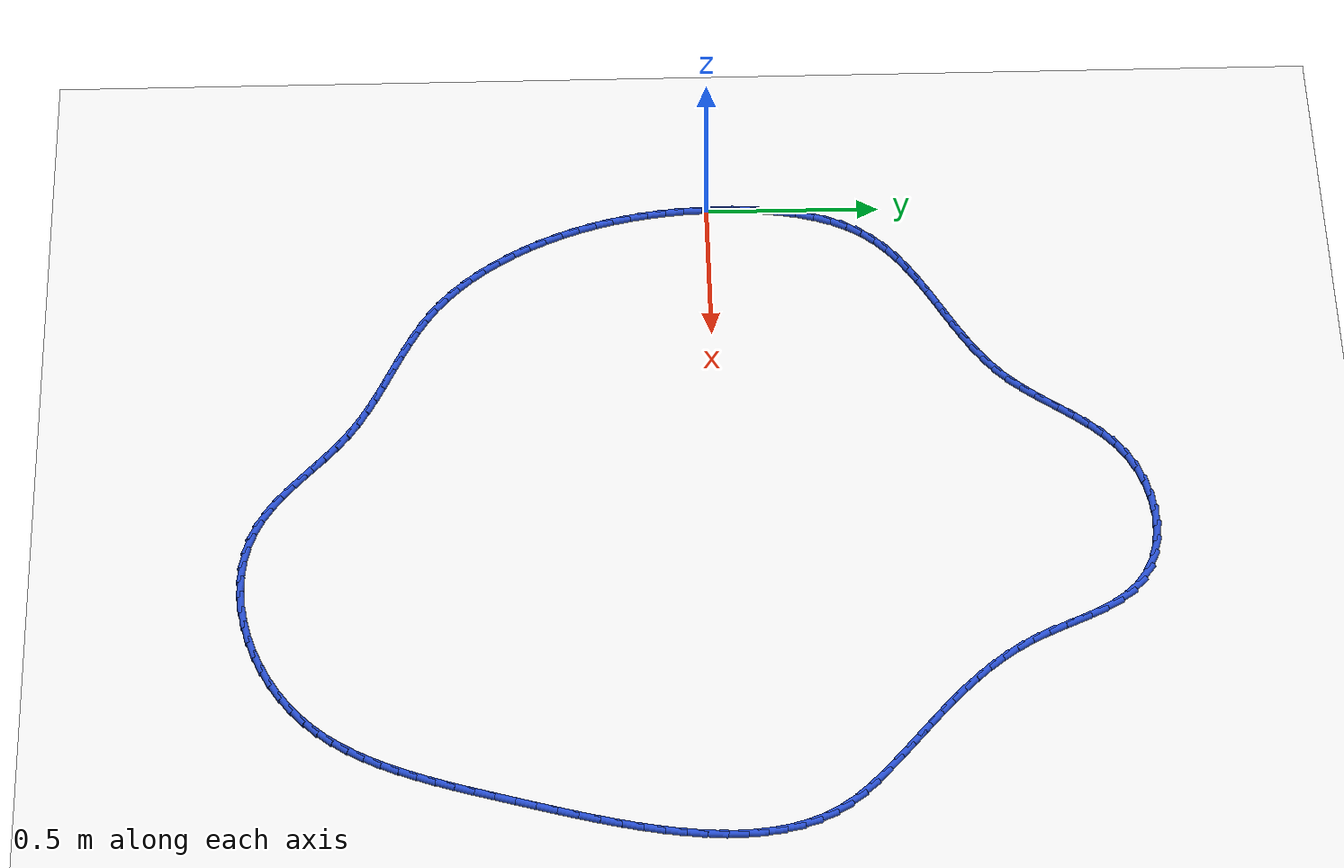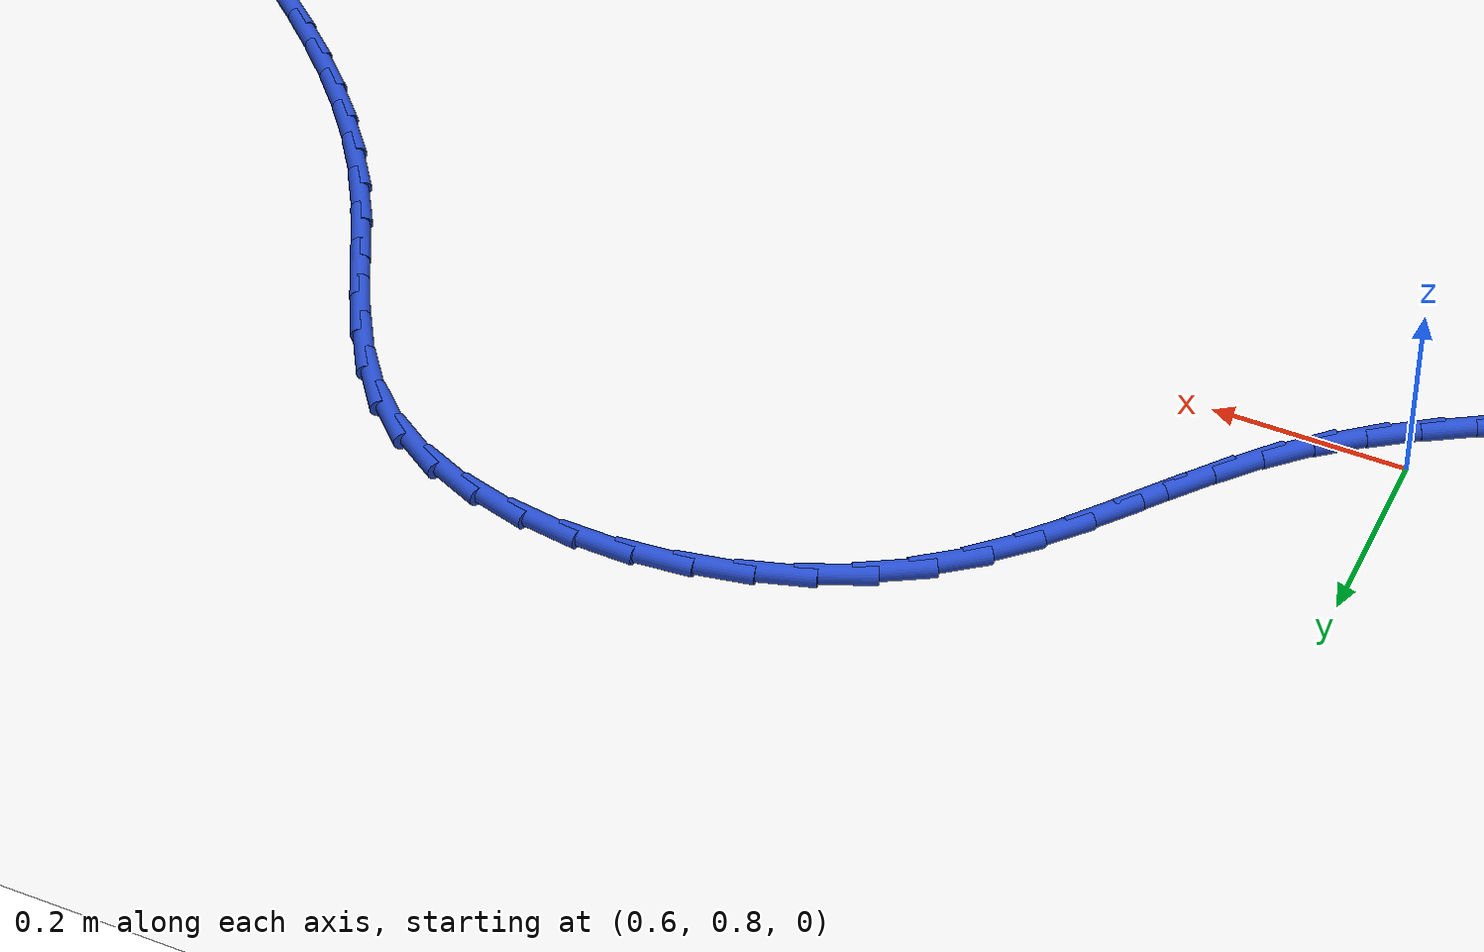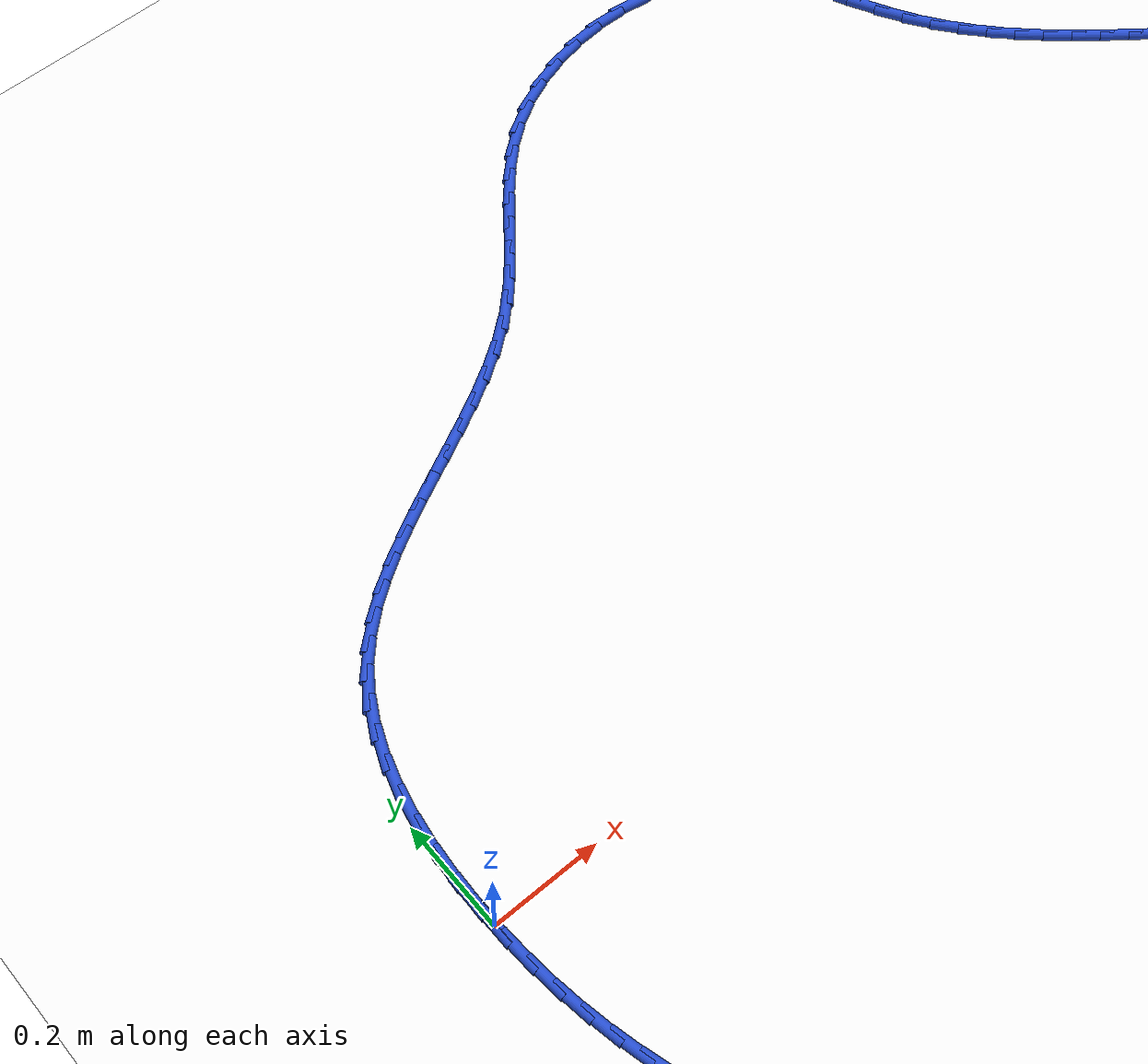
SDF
<sdf version="1.6">
 <world name="default">
  <light name="sun" type="directional">
   <pose>0 0 10 0 -0 0</pose>
   <diffuse>0.8 0.8 0.8 1</diffuse>
   <specular>0.2 0.2 0.2 1</specular>
   <attenuation>
    <range>1000</range>
    <constant>0.9</constant>
    <linear>0.01</linear>
    <quadratic>0.001</quadratic>
   </attenuation>
   <direction>-0.5 0.1 -0.9</direction>
  </light>
  <model name="ground_plane">
   <static>1</static>
   <link name="link">
    <collision name="collision">
     <geometry><plane><normal>0 0 1</normal><size>100 100</size></plane></geometry>
     <surface><friction><ode><mu>100</mu><mu2>50</mu2></ode></friction></surface>
    </collision>
    <visual name="visual">
     <cast_shadows>0</cast_shadows>
     <geometry><plane><normal>0 0 1</normal><size>100 100</size></plane></geometry>
     <material>
      <script><uri>file://media/materials/scripts/gazebo.material</uri><name>Gazebo/WhiteGlow</name></script>
     </material>
    </visual>
   </link>
  </model>
  <gravity>0 0 -9.8</gravity>
  <magnetic_field>6e-06 2.3e-05 -4.2e-05</magnetic_field>
  <atmosphere type="adiabatic"/>
  <physics name="default_physics" default="0" type="ode">
   <max_step_size>0.001</max_step_size>
   <real_time_factor>1</real_time_factor>
   <real_time_update_rate>1000</real_time_update_rate>
  </physics>
  <scene><ambient>0.4 0.4 0.4 1</ambient><background>0.7 0.7 0.7 1</background><shadows>1</shadows></scene>
  <spherical_coordinates>
   <surface_model>EARTH_WGS84</surface_model>
   <latitude_deg>0</latitude_deg>
   <longitude_deg>0</longitude_deg>
   <elevation>0</elevation>
   <heading_deg>0</heading_deg>
  </spherical_coordinates>
  <model name="line">
   <link name="link_0">
    <pose>-3.209238430557093e-17 -2.7755575615628914e-17 0.01 0 1.57 -1.5614146785968823</pose>
    <collision name="collision">
     <geometry><cylinder><radius>0.01</radius><length>0.08</length></cylinder></geometry>
    </collision>
    <visual name="visual">
     <material>
      <script><name>Gazebo/Blue</name><uri>file://media/materials/scripts/gazebo.material</uri></script>
     </material>
     <geometry><cylinder><radius>0.01</radius><length>0.08</length></cylinder></geometry>
    </visual>
   </link>
   <link name="link_1">
    <pose>-0.0005205562509979723 0.055485024338224574 0.01 0 1.57 1.5336357734559047</pose>
    <collision name="collision">
     <geometry><cylinder><radius>0.01</radius><length>0.08</length></cylinder></geometry>
    </collision>
    <visual name="visual">
     <material>
      <script><name>Gazebo/Blue</name><uri>file://media/materials/scripts/gazebo.material</uri></script>
     </material>
     <geometry><cylinder><radius>0.01</radius><length>0.08</length></cylinder></geometry>
    </visual>
   </link>
   <link name="link_2">
    <pose>0.001552704836371046 0.11125132722052263 0.01 0 1.57 1.4807161224466192</pose>
    <collision name="collision">
     <geometry><cylinder><radius>0.01</radius><length>0.08</length></cylinder></geometry>
    </collision>
    <visual name="visual">
     <material>
      <script><name>Gazebo/Blue</name><uri>file://media/materials/scripts/gazebo.material</uri></script>
     </material>
     <geometry><cylinder><radius>0.01</radius><length>0.08</length></cylinder></geometry>
    </visual>
   </link>
   <link name="link_3">
    <pose>0.006558838137702357 0.16667510590002396 0.01 0 1.57 1.4199414933770682</pose>
    <collision name="collision">
     <geometry><cylinder><radius>0.01</radius><length>0.08</length></cylinder></geometry>
    </collision>
    <visual name="visual">
     <material>
      <script><name>Gazebo/Blue</name><uri>file://media/materials/scripts/gazebo.material</uri></script>
     </material>
     <geometry><cylinder><radius>0.01</radius><length>0.08</length></cylinder></geometry>
    </visual>
   </link>
   <link name="link_4">
    <pose>0.014836898528591292 0.2211325576298585 0.01 0 1.57 1.349591802387273</pose>
    <collision name="collision">
     <geometry><cylinder><radius>0.01</radius><length>0.08</length></cylinder></geometry>
    </collision>
    <visual name="visual">
     <material>
      <script><name>Gazebo/Blue</name><uri>file://media/materials/scripts/gazebo.material</uri></script>
     </material>
     <geometry><cylinder><radius>0.01</radius><length>0.08</length></cylinder></geometry>
    </visual>
   </link>
   <link name="link_5">
    <pose>0.026725940884633204 0.2739998796631563 0.01 0 1.57 1.2677335016240336</pose>
    <collision name="collision">
     <geometry><cylinder><radius>0.01</radius><length>0.08</length></cylinder></geometry>
    </collision>
    <visual name="visual">
     <material>
      <script><name>Gazebo/Blue</name><uri>file://media/materials/scripts/gazebo.material</uri></script>
     </material>
     <geometry><cylinder><radius>0.01</radius><length>0.08</length></cylinder></geometry>
    </visual>
   </link>
   <link name="link_6">
    <pose>0.04256502008142346 0.32465326925304727 0.01 0 1.57 1.1723580194442573</pose>
    <collision name="collision">
     <geometry><cylinder><radius>0.01</radius><length>0.08</length></cylinder></geometry>
    </collision>
    <visual name="visual">
     <material>
      <script><name>Gazebo/Blue</name><uri>file://media/materials/scripts/gazebo.material</uri></script>
     </material>
     <geometry><cylinder><radius>0.01</radius><length>0.08</length></cylinder></geometry>
    </visual>
   </link>
   <link name="link_7">
    <pose>0.06269319099455734 0.3724689236526614 0.01 0 1.57 1.0617163003641088</pose>
    <collision name="collision">
     <geometry><cylinder><radius>0.01</radius><length>0.08</length></cylinder></geometry>
    </collision>
    <visual name="visual">
     <material>
      <script><name>Gazebo/Blue</name><uri>file://media/materials/scripts/gazebo.material</uri></script>
     </material>
     <geometry><cylinder><radius>0.01</radius><length>0.08</length></cylinder></geometry>
    </visual>
   </link>
   <link name="link_8">
    <pose>0.08744950849963024 0.4168230401151284 0.01 0 1.57 0.9359584628961841</pose>
    <collision name="collision">
     <geometry><cylinder><radius>0.01</radius><length>0.08</length></cylinder></geometry>
    </collision>
    <visual name="visual">
     <material>
      <script><name>Gazebo/Blue</name><uri>file://media/materials/scripts/gazebo.material</uri></script>
     </material>
     <geometry><cylinder><radius>0.01</radius><length>0.08</length></cylinder></geometry>
    </visual>
   </link>
   <link name="link_9">
    <pose>0.1171396823556434 0.45713278753878056 0.01 0 1.57 0.8124300084330521</pose>
    <collision name="collision">
     <geometry><cylinder><radius>0.01</radius><length>0.08</length></cylinder></geometry>
    </collision>
    <visual name="visual">
     <material>
      <script><name>Gazebo/Blue</name><uri>file://media/materials/scripts/gazebo.material</uri></script>
     </material>
     <geometry><cylinder><radius>0.01</radius><length>0.08</length></cylinder></geometry>
    </visual>
   </link>
   <link name="link_10">
    <pose>0.15154909743121658 0.4934546658237896 0.01 0 1.57 0.7070448001785046</pose>
    <collision name="collision">
     <geometry><cylinder><radius>0.01</radius><length>0.08</length></cylinder></geometry>
    </collision>
    <visual name="visual">
     <material>
      <script><name>Gazebo/Blue</name><uri>file://media/materials/scripts/gazebo.material</uri></script>
     </material>
     <geometry><cylinder><radius>0.01</radius><length>0.08</length></cylinder></geometry>
    </visual>
   </link>
   <link name="link_11">
    <pose>0.19005136541638057 0.5263511267547449 0.01 0 1.57 0.6214748167838323</pose>
    <collision name="collision">
     <geometry><cylinder><radius>0.01</radius><length>0.08</length></cylinder></geometry>
    </collision>
    <visual name="visual">
     <material>
      <script><name>Gazebo/Blue</name><uri>file://media/materials/scripts/gazebo.material</uri></script>
     </material>
     <geometry><cylinder><radius>0.01</radius><length>0.08</length></cylinder></geometry>
    </visual>
   </link>
   <link name="link_12">
    <pose>0.23200883649902734 0.556398459292926 0.01 0 1.57 0.5552211963426452</pose>
    <collision name="collision">
     <geometry><cylinder><radius>0.01</radius><length>0.08</length></cylinder></geometry>
    </collision>
    <visual name="visual">
     <material>
      <script><name>Gazebo/Blue</name><uri>file://media/materials/scripts/gazebo.material</uri></script>
     </material>
     <geometry><cylinder><radius>0.01</radius><length>0.08</length></cylinder></geometry>
    </visual>
   </link>
   <link name="link_13">
    <pose>0.27678386086704926 0.5841729523996128 0.01 0 1.57 0.5069662121934</pose>
    <collision name="collision">
     <geometry><cylinder><radius>0.01</radius><length>0.08</length></cylinder></geometry>
    </collision>
    <visual name="visual">
     <material>
      <script><name>Gazebo/Blue</name><uri>file://media/materials/scripts/gazebo.material</uri></script>
     </material>
     <geometry><cylinder><radius>0.01</radius><length>0.08</length></cylinder></geometry>
    </visual>
   </link>
   <link name="link_14">
    <pose>0.32373878870833805 0.6102508950360845 0.01 0 1.57 0.4752760883697195</pose>
    <collision name="collision">
     <geometry><cylinder><radius>0.01</radius><length>0.08</length></cylinder></geometry>
    </collision>
    <visual name="visual">
     <material>
      <script><name>Gazebo/Blue</name><uri>file://media/materials/scripts/gazebo.material</uri></script>
     </material>
     <geometry><cylinder><radius>0.01</radius><length>0.08</length></cylinder></geometry>
    </visual>
   </link>
   <link name="link_15">
    <pose>0.3722359702107862 0.6352085761636213 0.01 0 1.57 0.45898621706773857</pose>
    <collision name="collision">
     <geometry><cylinder><radius>0.01</radius><length>0.08</length></cylinder></geometry>
    </collision>
    <visual name="visual">
     <material>
      <script><name>Gazebo/Blue</name><uri>file://media/materials/scripts/gazebo.material</uri></script>
     </material>
     <geometry><cylinder><radius>0.01</radius><length>0.08</length></cylinder></geometry>
    </visual>
   </link>
   <link name="link_16">
    <pose>0.4216377555622856 0.6596222847435024 0.01 0 1.57 0.4573731121157386</pose>
    <collision name="collision">
     <geometry><cylinder><radius>0.01</radius><length>0.08</length></cylinder></geometry>
    </collision>
    <visual name="visual">
     <material>
      <script><name>Gazebo/Blue</name><uri>file://media/materials/scripts/gazebo.material</uri></script>
     </material>
     <geometry><cylinder><radius>0.01</radius><length>0.08</length></cylinder></geometry>
    </visual>
   </link>
   <link name="link_17">
    <pose>0.47130649495072846 0.6840683097370076 0.01 0 1.57 0.47020806818069877</pose>
    <collision name="collision">
     <geometry><cylinder><radius>0.01</radius><length>0.08</length></cylinder></geometry>
    </collision>
    <visual name="visual">
     <material>
      <script><name>Gazebo/Blue</name><uri>file://media/materials/scripts/gazebo.material</uri></script>
     </material>
     <geometry><cylinder><radius>0.01</radius><length>0.08</length></cylinder></geometry>
    </visual>
   </link>
   <link name="link_18">
    <pose>0.5206045385640068 0.7091229401054167 0.01 0 1.57 0.4977443730266458</pose>
    <collision name="collision">
     <geometry><cylinder><radius>0.01</radius><length>0.08</length></cylinder></geometry>
    </collision>
    <visual name="visual">
     <material>
      <script><name>Gazebo/Blue</name><uri>file://media/materials/scripts/gazebo.material</uri></script>
     </material>
     <geometry><cylinder><radius>0.01</radius><length>0.08</length></cylinder></geometry>
    </visual>
   </link>
   <link name="link_19">
    <pose>0.5688942365900129 0.7353624648100091 0.01 0 1.57 0.5406478338676475</pose>
    <collision name="collision">
     <geometry><cylinder><radius>0.01</radius><length>0.08</length></cylinder></geometry>
    </collision>
    <visual name="visual">
     <material>
      <script><name>Gazebo/Blue</name><uri>file://media/materials/scripts/gazebo.material</uri></script>
     </material>
     <geometry><cylinder><radius>0.01</radius><length>0.08</length></cylinder></geometry>
    </visual>
   </link>
   <link name="link_20">
    <pose>0.6155379392166385 0.7633631728120643 0.01 0 1.57 0.5998438492626406</pose>
    <collision name="collision">
     <geometry><cylinder><radius>0.01</radius><length>0.08</length></cylinder></geometry>
    </collision>
    <visual name="visual">
     <material>
      <script><name>Gazebo/Blue</name><uri>file://media/materials/scripts/gazebo.material</uri></script>
     </material>
     <geometry><cylinder><radius>0.01</radius><length>0.08</length></cylinder></geometry>
    </visual>
   </link>
   <link name="link_21">
    <pose>0.6598979966317762 0.7937013530728624 0.01 0 1.57 0.6762243494167626</pose>
    <collision name="collision">
     <geometry><cylinder><radius>0.01</radius><length>0.08</length></cylinder></geometry>
    </collision>
    <visual name="visual">
     <material>
      <script><name>Gazebo/Blue</name><uri>file://media/materials/scripts/gazebo.material</uri></script>
     </material>
     <geometry><cylinder><radius>0.01</radius><length>0.08</length></cylinder></geometry>
    </visual>
   </link>
   <link name="link_22">
    <pose>0.7013367590233177 0.8269532945536828 0.01 0 1.57 0.7662512962271709</pose>
    <collision name="collision">
     <geometry><cylinder><radius>0.01</radius><length>0.08</length></cylinder></geometry>
    </collision>
    <visual name="visual">
     <material>
      <script><name>Gazebo/Blue</name><uri>file://media/materials/scripts/gazebo.material</uri></script>
     </material>
     <geometry><cylinder><radius>0.01</radius><length>0.08</length></cylinder></geometry>
    </visual>
   </link>
   <link name="link_23">
    <pose>0.7393667247765066 0.8635541394446191 0.01 0 1.57 0.8397741431615209</pose>
    <collision name="collision">
     <geometry><cylinder><radius>0.01</radius><length>0.08</length></cylinder></geometry>
    </collision>
    <visual name="visual">
     <material>
      <script><name>Gazebo/Blue</name><uri>file://media/materials/scripts/gazebo.material</uri></script>
     </material>
     <geometry><cylinder><radius>0.01</radius><length>0.08</length></cylinder></geometry>
    </visual>
   </link>
   <link name="link_24">
    <pose>0.7746300123092579 0.9028771309380333 0.01 0 1.57 0.8827204094085778</pose>
    <collision name="collision">
     <geometry><cylinder><radius>0.01</radius><length>0.08</length></cylinder></geometry>
    </collision>
    <visual name="visual">
     <material>
      <script><name>Gazebo/Blue</name><uri>file://media/materials/scripts/gazebo.material</uri></script>
     </material>
     <geometry><cylinder><radius>0.01</radius><length>0.08</length></cylinder></geometry>
    </visual>
   </link>
   <link name="link_25">
    <pose>0.8082829446928788 0.9438121342847895 0.01 0 1.57 0.8952619379264949</pose>
    <collision name="collision">
     <geometry><cylinder><radius>0.01</radius><length>0.08</length></cylinder></geometry>
    </collision>
    <visual name="visual">
     <material>
      <script><name>Gazebo/Blue</name><uri>file://media/materials/scripts/gazebo.material</uri></script>
     </material>
     <geometry><cylinder><radius>0.01</radius><length>0.08</length></cylinder></geometry>
    </visual>
   </link>
   <link name="link_26">
    <pose>0.8414844448118042 0.9852465707821457 0.01 0 1.57 0.8776323635891689</pose>
    <collision name="collision">
     <geometry><cylinder><radius>0.01</radius><length>0.08</length></cylinder></geometry>
    </collision>
    <visual name="visual">
     <material>
      <script><name>Gazebo/Blue</name><uri>file://media/materials/scripts/gazebo.material</uri></script>
     </material>
     <geometry><cylinder><radius>0.01</radius><length>0.08</length></cylinder></geometry>
    </visual>
   </link>
   <link name="link_27">
    <pose>0.8753934355504674 1.0260678617273593 0.01 0 1.57 0.8297142529982583</pose>
    <collision name="collision">
     <geometry><cylinder><radius>0.01</radius><length>0.08</length></cylinder></geometry>
    </collision>
    <visual name="visual">
     <material>
      <script><name>Gazebo/Blue</name><uri>file://media/materials/scripts/gazebo.material</uri></script>
     </material>
     <geometry><cylinder><radius>0.01</radius><length>0.08</length></cylinder></geometry>
    </visual>
   </link>
   <link name="link_28">
    <pose>0.9111688397933033 1.065163428417688 0.01 0 1.57 0.7515243078582637</pose>
    <collision name="collision">
     <geometry><cylinder><radius>0.01</radius><length>0.08</length></cylinder></geometry>
    </collision>
    <visual name="visual">
     <material>
      <script><name>Gazebo/Blue</name><uri>file://media/materials/scripts/gazebo.material</uri></script>
     </material>
     <geometry><cylinder><radius>0.01</radius><length>0.08</length></cylinder></geometry>
    </visual>
   </link>
   <link name="link_29">
    <pose>0.9499695804247452 1.10142069215039 0.01 0 1.57 0.6445073177646926</pose>
    <collision name="collision">
     <geometry><cylinder><radius>0.01</radius><length>0.08</length></cylinder></geometry>
    </collision>
    <visual name="visual">
     <material>
      <script><name>Gazebo/Blue</name><uri>file://media/materials/scripts/gazebo.material</uri></script>
     </material>
     <geometry><cylinder><radius>0.01</radius><length>0.08</length></cylinder></geometry>
    </visual>
   </link>
   <link name="link_30">
    <pose>0.9929545803292275 1.1337270742227226 0.01 0 1.57 0.5175565829299796</pose>
    <collision name="collision">
     <geometry><cylinder><radius>0.01</radius><length>0.08</length></cylinder></geometry>
    </collision>
    <visual name="visual">
     <material>
      <script><name>Gazebo/Blue</name><uri>file://media/materials/scripts/gazebo.material</uri></script>
     </material>
     <geometry><cylinder><radius>0.01</radius><length>0.08</length></cylinder></geometry>
    </visual>
   </link>
   <link name="link_31">
    <pose>1.0409971290331534 1.1610787503493143 0.01 0 1.57 0.3972609409740882</pose>
    <collision name="collision">
     <geometry><cylinder><radius>0.01</radius><length>0.08</length></cylinder></geometry>
    </collision>
    <visual name="visual">
     <material>
      <script><name>Gazebo/Blue</name><uri>file://media/materials/scripts/gazebo.material</uri></script>
     </material>
     <geometry><cylinder><radius>0.01</radius><length>0.08</length></cylinder></geometry>
    </visual>
   </link>
   <link name="link_32">
    <pose>1.0934056670109984 1.183067709871356 0.01 0 1.57 0.2874267763622139</pose>
    <collision name="collision">
     <geometry><cylinder><radius>0.01</radius><length>0.08</length></cylinder></geometry>
    </collision>
    <visual name="visual">
     <material>
      <script><name>Gazebo/Blue</name><uri>file://media/materials/scripts/gazebo.material</uri></script>
     </material>
     <geometry><cylinder><radius>0.01</radius><length>0.08</length></cylinder></geometry>
    </visual>
   </link>
   <link name="link_33">
    <pose>1.1489554911547633 1.1994889356462266 0.01 0 1.57 0.18322525600787415</pose>
    <collision name="collision">
     <geometry><cylinder><radius>0.01</radius><length>0.08</length></cylinder></geometry>
    </collision>
    <visual name="visual">
     <material>
      <script><name>Gazebo/Blue</name><uri>file://media/materials/scripts/gazebo.material</uri></script>
     </material>
     <geometry><cylinder><radius>0.01</radius><length>0.08</length></cylinder></geometry>
    </visual>
   </link>
   <link name="link_34">
    <pose>1.2064214488750622 1.2101375816705808 0.01 0 1.57 0.08014888149802434</pose>
    <collision name="collision">
     <geometry><cylinder><radius>0.01</radius><length>0.08</length></cylinder></geometry>
    </collision>
    <visual name="visual">
     <material>
      <script><name>Gazebo/Blue</name><uri>file://media/materials/scripts/gazebo.material</uri></script>
     </material>
     <geometry><cylinder><radius>0.01</radius><length>0.08</length></cylinder></geometry>
    </visual>
   </link>
   <link name="link_35">
    <pose>1.2645783875825094 1.214808801941074 0.01 0 1.57 -0.026217159379498946</pose>
    <collision name="collision">
     <geometry><cylinder><radius>0.01</radius><length>0.08</length></cylinder></geometry>
    </collision>
    <visual name="visual">
     <material>
      <script><name>Gazebo/Blue</name><uri>file://media/materials/scripts/gazebo.material</uri></script>
     </material>
     <geometry><cylinder><radius>0.01</radius><length>0.08</length></cylinder></geometry>
    </visual>
   </link>
   <link name="link_36">
    <pose>1.3222011546877188 1.2132977504543603 0.01 0 1.57 -0.14045259051549788</pose>
    <collision name="collision">
     <geometry><cylinder><radius>0.01</radius><length>0.08</length></cylinder></geometry>
    </collision>
    <visual name="visual">
     <material>
      <script><name>Gazebo/Blue</name><uri>file://media/materials/scripts/gazebo.material</uri></script>
     </material>
     <geometry><cylinder><radius>0.01</radius><length>0.08</length></cylinder></geometry>
    </visual>
   </link>
   <link name="link_37">
    <pose>1.378064597601305 1.2053995812070954 0.01 0 1.57 -0.2674590836290405</pose>
    <collision name="collision">
     <geometry><cylinder><radius>0.01</radius><length>0.08</length></cylinder></geometry>
    </collision>
    <visual name="visual">
     <material>
      <script><name>Gazebo/Blue</name><uri>file://media/materials/scripts/gazebo.material</uri></script>
     </material>
     <geometry><cylinder><radius>0.01</radius><length>0.08</length></cylinder></geometry>
    </visual>
   </link>
   <link name="link_38">
    <pose>1.430943563733882 1.1909094481959344 0.01 0 1.57 -0.41230882356067794</pose>
    <collision name="collision">
     <geometry><cylinder><radius>0.01</radius><length>0.08</length></cylinder></geometry>
    </collision>
    <visual name="visual">
     <material>
      <script><name>Gazebo/Blue</name><uri>file://media/materials/scripts/gazebo.material</uri></script>
     </material>
     <geometry><cylinder><radius>0.01</radius><length>0.08</length></cylinder></geometry>
    </visual>
   </link>
   <link name="link_39">
    <pose>1.4796129004960654 1.1696225054175322 0.01 0 1.57 -0.5793958451532532</pose>
    <collision name="collision">
     <geometry><cylinder><radius>0.01</radius><length>0.08</length></cylinder></geometry>
    </collision>
    <visual name="visual">
     <material>
      <script><name>Gazebo/Blue</name><uri>file://media/materials/scripts/gazebo.material</uri></script>
     </material>
     <geometry><cylinder><radius>0.01</radius><length>0.08</length></cylinder></geometry>
    </visual>
   </link>
   <link name="link_40">
    <pose>1.5228474552984674 1.1413339068685437 0.01 0 1.57 -0.7629888693921749</pose>
    <collision name="collision">
     <geometry><cylinder><radius>0.01</radius><length>0.08</length></cylinder></geometry>
    </collision>
    <visual name="visual">
     <material>
      <script><name>Gazebo/Blue</name><uri>file://media/materials/scripts/gazebo.material</uri></script>
     </material>
     <geometry><cylinder><radius>0.01</radius><length>0.08</length></cylinder></geometry>
    </visual>
   </link>
   <link name="link_41">
    <pose>1.559747424344777 1.106051758923441 0.01 0 1.57 -0.9165399849671361</pose>
    <collision name="collision">
     <geometry><cylinder><radius>0.01</radius><length>0.08</length></cylinder></geometry>
    </collision>
    <visual name="visual">
     <material>
      <script><name>Gazebo/Blue</name><uri>file://media/materials/scripts/gazebo.material</uri></script>
     </material>
     <geometry><cylinder><radius>0.01</radius><length>0.08</length></cylinder></geometry>
    </visual>
   </link>
   <link name="link_42">
    <pose>1.5912447236465708 1.064983093838367 0.01 0 1.57 -1.0218100722397259</pose>
    <collision name="collision">
     <geometry><cylinder><radius>0.01</radius><length>0.08</length></cylinder></geometry>
    </collision>
    <visual name="visual">
     <material>
      <script><name>Gazebo/Blue</name><uri>file://media/materials/scripts/gazebo.material</uri></script>
     </material>
     <geometry><cylinder><radius>0.01</radius><length>0.08</length></cylinder></geometry>
    </visual>
   </link>
   <link name="link_43">
    <pose>1.6189117652239255 1.0197541713290272 0.01 0 1.57 -1.0818738497053646</pose>
    <collision name="collision">
     <geometry><cylinder><radius>0.01</radius><length>0.08</length></cylinder></geometry>
    </collision>
    <visual name="visual">
     <material>
      <script><name>Gazebo/Blue</name><uri>file://media/materials/scripts/gazebo.material</uri></script>
     </material>
     <geometry><cylinder><radius>0.01</radius><length>0.08</length></cylinder></geometry>
    </visual>
   </link>
   <link name="link_44">
    <pose>1.6443216359157502 0.9719916928040988 0.01 0 1.57 -1.1007403865240946</pose>
    <collision name="collision">
     <geometry><cylinder><radius>0.01</radius><length>0.08</length></cylinder></geometry>
    </collision>
    <visual name="visual">
     <material>
      <script><name>Gazebo/Blue</name><uri>file://media/materials/scripts/gazebo.material</uri></script>
     </material>
     <geometry><cylinder><radius>0.01</radius><length>0.08</length></cylinder></geometry>
    </visual>
   </link>
   <link name="link_45">
    <pose>1.6690474225609546 0.9233223596722601 0.01 0 1.57 -1.0801616823141802</pose>
    <collision name="collision">
     <geometry><cylinder><radius>0.01</radius><length>0.08</length></cylinder></geometry>
    </collision>
    <visual name="visual">
     <material>
      <script><name>Gazebo/Blue</name><uri>file://media/materials/scripts/gazebo.material</uri></script>
     </material>
     <geometry><cylinder><radius>0.01</radius><length>0.08</length></cylinder></geometry>
    </visual>
   </link>
   <link name="link_46">
    <pose>1.6946622119984491 0.8753728733421883 0.01 0 1.57 -1.0205826761909955</pose>
    <collision name="collision">
     <geometry><cylinder><radius>0.01</radius><length>0.08</length></cylinder></geometry>
    </collision>
    <visual name="visual">
     <material>
      <script><name>Gazebo/Blue</name><uri>file://media/materials/scripts/gazebo.material</uri></script>
     </material>
     <geometry><cylinder><radius>0.01</radius><length>0.08</length></cylinder></geometry>
    </visual>
   </link>
   <link name="link_47">
    <pose>1.722675600399228 0.8297037759648401 0.01 0 1.57 -0.9460123651644902</pose>
    <collision name="collision">
     <geometry><cylinder><radius>0.01</radius><length>0.08</length></cylinder></geometry>
    </collision>
    <visual name="visual">
     <material>
      <script><name>Gazebo/Blue</name><uri>file://media/materials/scripts/gazebo.material</uri></script>
     </material>
     <geometry><cylinder><radius>0.01</radius><length>0.08</length></cylinder></geometry>
    </visual>
   </link>
   <link name="link_48">
    <pose>1.753594053122094 0.7868303160738275 0.01 0 1.57 -0.8780204696650113</pose>
    <collision name="collision">
     <geometry><cylinder><radius>0.01</radius><length>0.08</length></cylinder></geometry>
    </collision>
    <visual name="visual">
     <material>
      <script><name>Gazebo/Blue</name><uri>file://media/materials/scripts/gazebo.material</uri></script>
     </material>
     <geometry><cylinder><radius>0.01</radius><length>0.08</length></cylinder></geometry>
    </visual>
   </link>
   <link name="link_49">
    <pose>1.787123719113368 0.7464337875204291 0.01 0 1.57 -0.8182772562882528</pose>
    <collision name="collision">
     <geometry><cylinder><radius>0.01</radius><length>0.08</length></cylinder></geometry>
    </collision>
    <visual name="visual">
     <material>
      <script><name>Gazebo/Blue</name><uri>file://media/materials/scripts/gazebo.material</uri></script>
     </material>
     <geometry><cylinder><radius>0.01</radius><length>0.08</length></cylinder></geometry>
    </visual>
   </link>
   <link name="link_50">
    <pose>1.822948469370452 0.7081722698377785 0.01 0 1.57 -0.7674219136471415</pose>
    <collision name="collision">
     <geometry><cylinder><radius>0.01</radius><length>0.08</length></cylinder></geometry>
    </collision>
    <visual name="visual">
     <material>
      <script><name>Gazebo/Blue</name><uri>file://media/materials/scripts/gazebo.material</uri></script>
     </material>
     <geometry><cylinder><radius>0.01</radius><length>0.08</length></cylinder></geometry>
    </visual>
   </link>
   <link name="link_51">
    <pose>1.8607521748907452 0.6717038425590107 0.01 0 1.57 -0.7257342585869346</pose>
    <collision name="collision">
     <geometry><cylinder><radius>0.01</radius><length>0.08</length></cylinder></geometry>
    </collision>
    <visual name="visual">
     <material>
      <script><name>Gazebo/Blue</name><uri>file://media/materials/scripts/gazebo.material</uri></script>
     </material>
     <geometry><cylinder><radius>0.01</radius><length>0.08</length></cylinder></geometry>
    </visual>
   </link>
   <link name="link_52">
    <pose>1.90021870667165 0.636686585217259 0.01 0 1.57 -0.6932467980313803</pose>
    <collision name="collision">
     <geometry><cylinder><radius>0.01</radius><length>0.08</length></cylinder></geometry>
    </collision>
    <visual name="visual">
     <material>
      <script><name>Gazebo/Blue</name><uri>file://media/materials/scripts/gazebo.material</uri></script>
     </material>
     <geometry><cylinder><radius>0.01</radius><length>0.08</length></cylinder></geometry>
    </visual>
   </link>
   <link name="link_53">
    <pose>1.9410319357105663 0.6027785773456585 0.01 0 1.57 -0.6698495700601332</pose>
    <collision name="collision">
     <geometry><cylinder><radius>0.01</radius><length>0.08</length></cylinder></geometry>
    </collision>
    <visual name="visual">
     <material>
      <script><name>Gazebo/Blue</name><uri>file://media/materials/scripts/gazebo.material</uri></script>
     </material>
     <geometry><cylinder><radius>0.01</radius><length>0.08</length></cylinder></geometry>
    </visual>
   </link>
   <link name="link_54">
    <pose>1.9828757330048945 0.569637898477343 0.01 0 1.57 -0.6553732182516595</pose>
    <collision name="collision">
     <geometry><cylinder><radius>0.01</radius><length>0.08</length></cylinder></geometry>
    </collision>
    <visual name="visual">
     <material>
      <script><name>Gazebo/Blue</name><uri>file://media/materials/scripts/gazebo.material</uri></script>
     </material>
     <geometry><cylinder><radius>0.01</radius><length>0.08</length></cylinder></geometry>
    </visual>
   </link>
   <link name="link_55">
    <pose>2.025433969552037 0.5369226281454463 0.01 0 1.57 -0.6496462161907598</pose>
    <collision name="collision">
     <geometry><cylinder><radius>0.01</radius><length>0.08</length></cylinder></geometry>
    </collision>
    <visual name="visual">
     <material>
      <script><name>Gazebo/Blue</name><uri>file://media/materials/scripts/gazebo.material</uri></script>
     </material>
     <geometry><cylinder><radius>0.01</radius><length>0.08</length></cylinder></geometry>
    </visual>
   </link>
   <link name="link_56">
    <pose>2.068390516349393 0.5042908458831037 0.01 0 1.57 -0.6525276133169537</pose>
    <collision name="collision">
     <geometry><cylinder><radius>0.01</radius><length>0.08</length></cylinder></geometry>
    </collision>
    <visual name="visual">
     <material>
      <script><name>Gazebo/Blue</name><uri>file://media/materials/scripts/gazebo.material</uri></script>
     </material>
     <geometry><cylinder><radius>0.01</radius><length>0.08</length></cylinder></geometry>
    </visual>
   </link>
   <link name="link_57">
    <pose>2.1114292443943645 0.47140063122344816 0.01 0 1.57 -0.6639183233076539</pose>
    <collision name="collision">
     <geometry><cylinder><radius>0.01</radius><length>0.08</length></cylinder></geometry>
    </collision>
    <visual name="visual">
     <material>
      <script><name>Gazebo/Blue</name><uri>file://media/materials/scripts/gazebo.material</uri></script>
     </material>
     <geometry><cylinder><radius>0.01</radius><length>0.08</length></cylinder></geometry>
    </visual>
   </link>
   <link name="link_58">
    <pose>2.154234021318339 0.4379100634044573 0.01 0 1.57 -0.6863994606707727</pose>
    <collision name="collision">
     <geometry><cylinder><radius>0.01</radius><length>0.08</length></cylinder></geometry>
    </collision>
    <visual name="visual">
     <material>
      <script><name>Gazebo/Blue</name><uri>file://media/materials/scripts/gazebo.material</uri></script>
     </material>
     <geometry><cylinder><radius>0.01</radius><length>0.08</length></cylinder></geometry>
    </visual>
   </link>
   <link name="link_59">
    <pose>2.196283127843759 0.4034591942544183 0.01 0 1.57 -0.7304318759320905</pose>
    <collision name="collision">
     <geometry><cylinder><radius>0.01</radius><length>0.08</length></cylinder></geometry>
    </collision>
    <visual name="visual">
     <material>
      <script><name>Gazebo/Blue</name><uri>file://media/materials/scripts/gazebo.material</uri></script>
     </material>
     <geometry><cylinder><radius>0.01</radius><length>0.08</length></cylinder></geometry>
    </visual>
   </link>
   <link name="link_60">
    <pose>2.2362942783079824 0.3676213834085697 0.01 0 1.57 -0.8009228601122274</pose>
    <collision name="collision">
     <geometry><cylinder><radius>0.01</radius><length>0.08</length></cylinder></geometry>
    </collision>
    <visual name="visual">
     <material>
      <script><name>Gazebo/Blue</name><uri>file://media/materials/scripts/gazebo.material</uri></script>
     </material>
     <geometry><cylinder><radius>0.01</radius><length>0.08</length></cylinder></geometry>
    </visual>
   </link>
   <link name="link_61">
    <pose>2.272809346515641 0.32995457147892565 0.01 0 1.57 -0.9019165357560492</pose>
    <collision name="collision">
     <geometry><cylinder><radius>0.01</radius><length>0.08</length></cylinder></geometry>
    </collision>
    <visual name="visual">
     <material>
      <script><name>Gazebo/Blue</name><uri>file://media/materials/scripts/gazebo.material</uri></script>
     </material>
     <geometry><cylinder><radius>0.01</radius><length>0.08</length></cylinder></geometry>
    </visual>
   </link>
   <link name="link_62">
    <pose>2.304375941757252 0.2900187177753706 0.01 0 1.57 -1.0251819050125464</pose>
    <collision name="collision">
     <geometry><cylinder><radius>0.01</radius><length>0.08</length></cylinder></geometry>
    </collision>
    <visual name="visual">
     <material>
      <script><name>Gazebo/Blue</name><uri>file://media/materials/scripts/gazebo.material</uri></script>
     </material>
     <geometry><cylinder><radius>0.01</radius><length>0.08</length></cylinder></geometry>
    </visual>
   </link>
   <link name="link_63">
    <pose>2.3301377684848146 0.24758358702899258 0.01 0 1.57 -1.1468155536647162</pose>
    <collision name="collision">
     <geometry><cylinder><radius>0.01</radius><length>0.08</length></cylinder></geometry>
    </collision>
    <visual name="visual">
     <material>
      <script><name>Gazebo/Blue</name><uri>file://media/materials/scripts/gazebo.material</uri></script>
     </material>
     <geometry><cylinder><radius>0.01</radius><length>0.08</length></cylinder></geometry>
    </visual>
   </link>
   <link name="link_64">
    <pose>2.350346995640582 0.2028090861399407 0.01 0 1.57 -1.260747888259988</pose>
    <collision name="collision">
     <geometry><cylinder><radius>0.01</radius><length>0.08</length></cylinder></geometry>
    </collision>
    <visual name="visual">
     <material>
      <script><name>Gazebo/Blue</name><uri>file://media/materials/scripts/gazebo.material</uri></script>
     </material>
     <geometry><cylinder><radius>0.01</radius><length>0.08</length></cylinder></geometry>
    </visual>
   </link>
   <link name="link_65">
    <pose>2.3653765343338704 0.15589761918474596 0.01 0 1.57 -1.364488635618397</pose>
    <collision name="collision">
     <geometry><cylinder><radius>0.01</radius><length>0.08</length></cylinder></geometry>
    </collision>
    <visual name="visual">
     <material>
      <script><name>Gazebo/Blue</name><uri>file://media/materials/scripts/gazebo.material</uri></script>
     </material>
     <geometry><cylinder><radius>0.01</radius><length>0.08</length></cylinder></geometry>
    </visual>
   </link>
   <link name="link_66">
    <pose>2.3755992956739993 0.10705159023993915 0.01 0 1.57 -1.4568378301633322</pose>
    <collision name="collision">
     <geometry><cylinder><radius>0.01</radius><length>0.08</length></cylinder></geometry>
    </collision>
    <visual name="visual">
     <material>
      <script><name>Gazebo/Blue</name><uri>file://media/materials/scripts/gazebo.material</uri></script>
     </material>
     <geometry><cylinder><radius>0.01</radius><length>0.08</length></cylinder></geometry>
    </visual>
   </link>
   <link name="link_67">
    <pose>2.381388190770284 0.056473403382052256 0.01 0 1.57 -1.5376476936461079</pose>
    <collision name="collision">
     <geometry><cylinder><radius>0.01</radius><length>0.08</length></cylinder></geometry>
    </collision>
    <visual name="visual">
     <material>
      <script><name>Gazebo/Blue</name><uri>file://media/materials/scripts/gazebo.material</uri></script>
     </material>
     <geometry><cylinder><radius>0.01</radius><length>0.08</length></cylinder></geometry>
    </visual>
   </link>
   <link name="link_68">
    <pose>2.383116130732043 0.0043654626876157045 0.01 0 1.57 1.5341309393264688</pose>
    <collision name="collision">
     <geometry><cylinder><radius>0.01</radius><length>0.08</length></cylinder></geometry>
    </collision>
    <visual name="visual">
     <material>
      <script><name>Gazebo/Blue</name><uri>file://media/materials/scripts/gazebo.material</uri></script>
     </material>
     <geometry><cylinder><radius>0.01</radius><length>0.08</length></cylinder></geometry>
    </visual>
   </link>
   <link name="link_69">
    <pose>2.381156026668595 -0.04906982776683835 0.01 0 1.57 1.474409455700609</pose>
    <collision name="collision">
     <geometry><cylinder><radius>0.01</radius><length>0.08</length></cylinder></geometry>
    </collision>
    <visual name="visual">
     <material>
      <script><name>Gazebo/Blue</name><uri>file://media/materials/scripts/gazebo.material</uri></script>
     </material>
     <geometry><cylinder><radius>0.01</radius><length>0.08</length></cylinder></geometry>
    </visual>
   </link>
   <link name="link_70">
    <pose>2.3758807896892558 -0.10363006390477958 0.01 0 1.57 1.4237569834721724</pose>
    <collision name="collision">
     <geometry><cylinder><radius>0.01</radius><length>0.08</length></cylinder></geometry>
    </collision>
    <visual name="visual">
     <material>
      <script><name>Gazebo/Blue</name><uri>file://media/materials/scripts/gazebo.material</uri></script>
     </material>
     <geometry><cylinder><radius>0.01</radius><length>0.08</length></cylinder></geometry>
    </visual>
   </link>
   <link name="link_71">
    <pose>2.367663330903344 -0.1591128416496759 0.01 0 1.57 1.3811766807937929</pose>
    <collision name="collision">
     <geometry><cylinder><radius>0.01</radius><length>0.08</length></cylinder></geometry>
    </collision>
    <visual name="visual">
     <material>
      <script><name>Gazebo/Blue</name><uri>file://media/materials/scripts/gazebo.material</uri></script>
     </material>
     <geometry><cylinder><radius>0.01</radius><length>0.08</length></cylinder></geometry>
    </visual>
   </link>
   <link name="link_72">
    <pose>2.356876561420177 -0.21531575692499644 0.01 0 1.57 1.345776062920202</pose>
    <collision name="collision">
     <geometry><cylinder><radius>0.01</radius><length>0.08</length></cylinder></geometry>
    </collision>
    <visual name="visual">
     <material>
      <script><name>Gazebo/Blue</name><uri>file://media/materials/scripts/gazebo.material</uri></script>
     </material>
     <geometry><cylinder><radius>0.01</radius><length>0.08</length></cylinder></geometry>
    </visual>
   </link>
   <link name="link_73">
    <pose>2.343893392349072 -0.27203640565421106 0.01 0 1.57 1.3168010446661833</pose>
    <collision name="collision">
     <geometry><cylinder><radius>0.01</radius><length>0.08</length></cylinder></geometry>
    </collision>
    <visual name="visual">
     <material>
      <script><name>Gazebo/Blue</name><uri>file://media/materials/scripts/gazebo.material</uri></script>
     </material>
     <geometry><cylinder><radius>0.01</radius><length>0.08</length></cylinder></geometry>
    </visual>
   </link>
   <link name="link_74">
    <pose>2.329086734799347 -0.32907238376078646 0.01 0 1.57 1.2936460247527384</pose>
    <collision name="collision">
     <geometry><cylinder><radius>0.01</radius><length>0.08</length></cylinder></geometry>
    </collision>
    <visual name="visual">
     <material>
      <script><name>Gazebo/Blue</name><uri>file://media/materials/scripts/gazebo.material</uri></script>
     </material>
     <geometry><cylinder><radius>0.01</radius><length>0.08</length></cylinder></geometry>
    </visual>
   </link>
   <link name="link_75">
    <pose>2.3128294998803196 -0.3862212871681925 0.01 0 1.57 1.2758529715067264</pose>
    <collision name="collision">
     <geometry><cylinder><radius>0.01</radius><length>0.08</length></cylinder></geometry>
    </collision>
    <visual name="visual">
     <material>
      <script><name>Gazebo/Blue</name><uri>file://media/materials/scripts/gazebo.material</uri></script>
     </material>
     <geometry><cylinder><radius>0.01</radius><length>0.08</length></cylinder></geometry>
    </visual>
   </link>
   <link name="link_76">
    <pose>2.295494598701307 -0.4432807117998978 0.01 0 1.57 1.2631073957252397</pose>
    <collision name="collision">
     <geometry><cylinder><radius>0.01</radius><length>0.08</length></cylinder></geometry>
    </collision>
    <visual name="visual">
     <material>
      <script><name>Gazebo/Blue</name><uri>file://media/materials/scripts/gazebo.material</uri></script>
     </material>
     <geometry><cylinder><radius>0.01</radius><length>0.08</length></cylinder></geometry>
    </visual>
   </link>
   <link name="link_77">
    <pose>2.277454942371627 -0.5000482535793713 0.01 0 1.57 1.255235905991164</pose>
    <collision name="collision">
     <geometry><cylinder><radius>0.01</radius><length>0.08</length></cylinder></geometry>
    </collision>
    <visual name="visual">
     <material>
      <script><name>Gazebo/Blue</name><uri>file://media/materials/scripts/gazebo.material</uri></script>
     </material>
     <geometry><cylinder><radius>0.01</radius><length>0.08</length></cylinder></geometry>
    </visual>
   </link>
   <link name="link_78">
    <pose>2.259083442000596 -0.5563215084300823 0.01 0 1.57 1.2521747867328303</pose>
    <collision name="collision">
     <geometry><cylinder><radius>0.01</radius><length>0.08</length></cylinder></geometry>
    </collision>
    <visual name="visual">
     <material>
      <script><name>Gazebo/Blue</name><uri>file://media/materials/scripts/gazebo.material</uri></script>
     </material>
     <geometry><cylinder><radius>0.01</radius><length>0.08</length></cylinder></geometry>
    </visual>
   </link>
   <link name="link_79">
    <pose>2.240750900182173 -0.6118981993489769 0.01 0 1.57 1.250223973457178</pose>
    <collision name="collision">
     <geometry><cylinder><radius>0.01</radius><length>0.08</length></cylinder></geometry>
    </collision>
    <visual name="visual">
     <material>
      <script><name>Gazebo/Blue</name><uri>file://media/materials/scripts/gazebo.material</uri></script>
     </material>
     <geometry><cylinder><radius>0.01</radius><length>0.08</length></cylinder></geometry>
    </visual>
   </link>
   <link name="link_80">
    <pose>2.222591772240053 -0.6665902932272237 0.01 0 1.57 1.2420441650758764</pose>
    <collision name="collision">
     <geometry><cylinder><radius>0.01</radius><length>0.08</length></cylinder></geometry>
    </collision>
    <visual name="visual">
     <material>
      <script><name>Gazebo/Blue</name><uri>file://media/materials/scripts/gazebo.material</uri></script>
     </material>
     <geometry><cylinder><radius>0.01</radius><length>0.08</length></cylinder></geometry>
    </visual>
   </link>
   <link name="link_81">
    <pose>2.2042912628705182 -0.7202368318547563 0.01 0 1.57 1.2264657313856089</pose>
    <collision name="collision">
     <geometry><cylinder><radius>0.01</radius><length>0.08</length></cylinder></geometry>
    </collision>
    <visual name="visual">
     <material>
      <script><name>Gazebo/Blue</name><uri>file://media/materials/scripts/gazebo.material</uri></script>
     </material>
     <geometry><cylinder><radius>0.01</radius><length>0.08</length></cylinder></geometry>
    </visual>
   </link>
   <link name="link_82">
    <pose>2.1854842987482375 -0.7726798871170997 0.01 0 1.57 1.2030818967663814</pose>
    <collision name="collision">
     <geometry><cylinder><radius>0.01</radius><length>0.08</length></cylinder></geometry>
    </collision>
    <visual name="visual">
     <material>
      <script><name>Gazebo/Blue</name><uri>file://media/materials/scripts/gazebo.material</uri></script>
     </material>
     <geometry><cylinder><radius>0.01</radius><length>0.08</length></cylinder></geometry>
    </visual>
   </link>
   <link name="link_83">
    <pose>2.16580580654788 -0.8237615308997753 0.01 0 1.57 1.171472852142143</pose>
    <collision name="collision">
     <geometry><cylinder><radius>0.01</radius><length>0.08</length></cylinder></geometry>
    </collision>
    <visual name="visual">
     <material>
      <script><name>Gazebo/Blue</name><uri>file://media/materials/scripts/gazebo.material</uri></script>
     </material>
     <geometry><cylinder><radius>0.01</radius><length>0.08</length></cylinder></geometry>
    </visual>
   </link>
   <link name="link_84">
    <pose>2.1448907129441164 -0.8733238350883091 0.01 0 1.57 1.1312507025252598</pose>
    <collision name="collision">
     <geometry><cylinder><radius>0.01</radius><length>0.08</length></cylinder></geometry>
    </collision>
    <visual name="visual">
     <material>
      <script><name>Gazebo/Blue</name><uri>file://media/materials/scripts/gazebo.material</uri></script>
     </material>
     <geometry><cylinder><radius>0.01</radius><length>0.08</length></cylinder></geometry>
    </visual>
   </link>
   <link name="link_85">
    <pose>2.1223739446116148 -0.9212088715682243 0.01 0 1.57 1.0821315320911233</pose>
    <collision name="collision">
     <geometry><cylinder><radius>0.01</radius><length>0.08</length></cylinder></geometry>
    </collision>
    <visual name="visual">
     <material>
      <script><name>Gazebo/Blue</name><uri>file://media/materials/scripts/gazebo.material</uri></script>
     </material>
     <geometry><cylinder><radius>0.01</radius><length>0.08</length></cylinder></geometry>
    </visual>
   </link>
   <link name="link_86">
    <pose>2.0978904282250457 -0.9672587122250451 0.01 0 1.57 1.024037200661404</pose>
    <collision name="collision">
     <geometry><cylinder><radius>0.01</radius><length>0.08</length></cylinder></geometry>
    </collision>
    <visual name="visual">
     <material>
      <script><name>Gazebo/Blue</name><uri>file://media/materials/scripts/gazebo.material</uri></script>
     </material>
     <geometry><cylinder><radius>0.01</radius><length>0.08</length></cylinder></geometry>
    </visual>
   </link>
   <link name="link_87">
    <pose>2.0710750904590776 -1.011315428944296 0.01 0 1.57 0.9572210229566452</pose>
    <collision name="collision">
     <geometry><cylinder><radius>0.01</radius><length>0.08</length></cylinder></geometry>
    </collision>
    <visual name="visual">
     <material>
      <script><name>Gazebo/Blue</name><uri>file://media/materials/scripts/gazebo.material</uri></script>
     </material>
     <geometry><cylinder><radius>0.01</radius><length>0.08</length></cylinder></geometry>
    </visual>
   </link>
   <link name="link_88">
    <pose>2.0415628579883798 -1.0532210936114996 0.01 0 1.57 0.8823963661831999</pose>
    <collision name="collision">
     <geometry><cylinder><radius>0.01</radius><length>0.08</length></cylinder></geometry>
    </collision>
    <visual name="visual">
     <material>
      <script><name>Gazebo/Blue</name><uri>file://media/materials/scripts/gazebo.material</uri></script>
     </material>
     <geometry><cylinder><radius>0.01</radius><length>0.08</length></cylinder></geometry>
    </visual>
   </link>
   <link name="link_89">
    <pose>2.0089886574876235 -1.0928177781121808 0.01 0 1.57 0.8008286171803642</pose>
    <collision name="collision">
     <geometry><cylinder><radius>0.01</radius><length>0.08</length></cylinder></geometry>
    </collision>
    <visual name="visual">
     <material>
      <script><name>Gazebo/Blue</name><uri>file://media/materials/scripts/gazebo.material</uri></script>
     </material>
     <geometry><cylinder><radius>0.01</radius><length>0.08</length></cylinder></geometry>
    </visual>
   </link>
   <link name="link_90">
    <pose>1.9729874156314773 -1.1299475543318638 0.01 0 1.57 0.71444885028179</pose>
    <collision name="collision">
     <geometry><cylinder><radius>0.01</radius><length>0.08</length></cylinder></geometry>
    </collision>
    <visual name="visual">
     <material>
      <script><name>Gazebo/Blue</name><uri>file://media/materials/scripts/gazebo.material</uri></script>
     </material>
     <geometry><cylinder><radius>0.01</radius><length>0.08</length></cylinder></geometry>
    </visual>
   </link>
   <link name="link_91">
    <pose>1.9332031402578094 -1.1644522186441424 0.01 0 1.57 0.6291782686108669</pose>
    <collision name="collision">
     <geometry><cylinder><radius>0.01</radius><length>0.08</length></cylinder></geometry>
    </collision>
    <visual name="visual">
     <material>
      <script><name>Gazebo/Blue</name><uri>file://media/materials/scripts/gazebo.material</uri></script>
     </material>
     <geometry><cylinder><radius>0.01</radius><length>0.08</length></cylinder></geometry>
    </visual>
   </link>
   <link name="link_92">
    <pose>1.889636144650913 -1.1961627575297622 0.01 0 1.57 0.5498151848511597</pose>
    <collision name="collision">
     <geometry><cylinder><radius>0.01</radius><length>0.08</length></cylinder></geometry>
    </collision>
    <visual name="visual">
     <material>
      <script><name>Gazebo/Blue</name><uri>file://media/materials/scripts/gazebo.material</uri></script>
     </material>
     <geometry><cylinder><radius>0.01</radius><length>0.08</length></cylinder></geometry>
    </visual>
   </link>
   <link name="link_93">
    <pose>1.8427514992066685 -1.2248960572792333 0.01 0 1.57 0.4751527818619786</pose>
    <collision name="collision">
     <geometry><cylinder><radius>0.01</radius><length>0.08</length></cylinder></geometry>
    </collision>
    <visual name="visual">
     <material>
      <script><name>Gazebo/Blue</name><uri>file://media/materials/scripts/gazebo.material</uri></script>
     </material>
     <geometry><cylinder><radius>0.01</radius><length>0.08</length></cylinder></geometry>
    </visual>
   </link>
   <link name="link_94">
    <pose>1.793045527062539 -1.2504680560112338 0.01 0 1.57 0.4037163862183464</pose>
    <collision name="collision">
     <geometry><cylinder><radius>0.01</radius><length>0.08</length></cylinder></geometry>
    </collision>
    <visual name="visual">
     <material>
      <script><name>Gazebo/Blue</name><uri>file://media/materials/scripts/gazebo.material</uri></script>
     </material>
     <geometry><cylinder><radius>0.01</radius><length>0.08</length></cylinder></geometry>
    </visual>
   </link>
   <link name="link_95">
    <pose>1.7410145513559871 -1.2726946918444426 0.01 0 1.57 0.33413079787318184</pose>
    <collision name="collision">
     <geometry><cylinder><radius>0.01</radius><length>0.08</length></cylinder></geometry>
    </collision>
    <visual name="visual">
     <material>
      <script><name>Gazebo/Blue</name><uri>file://media/materials/scripts/gazebo.material</uri></script>
     </material>
     <geometry><cylinder><radius>0.01</radius><length>0.08</length></cylinder></geometry>
    </visual>
   </link>
   <link name="link_96">
    <pose>1.6871548952244766 -1.291391902897537 0.01 0 1.57 0.2650940763172892</pose>
    <collision name="collision">
     <geometry><cylinder><radius>0.01</radius><length>0.08</length></cylinder></geometry>
    </collision>
    <visual name="visual">
     <material>
      <script><name>Gazebo/Blue</name><uri>file://media/materials/scripts/gazebo.material</uri></script>
     </material>
     <geometry><cylinder><radius>0.01</radius><length>0.08</length></cylinder></geometry>
    </visual>
   </link>
   <link name="link_97">
    <pose>1.6319628818054706 -1.3063756272891958 0.01 0 1.57 0.19534503331969222</pose>
    <collision name="collision">
     <geometry><cylinder><radius>0.01</radius><length>0.08</length></cylinder></geometry>
    </collision>
    <visual name="visual">
     <material>
      <script><name>Gazebo/Blue</name><uri>file://media/materials/scripts/gazebo.material</uri></script>
     </material>
     <geometry><cylinder><radius>0.01</radius><length>0.08</length></cylinder></geometry>
    </visual>
   </link>
   <link name="link_98">
    <pose>1.5759348342364312 -1.3174618031380967 0.01 0 1.57 0.12363168947009534</pose>
    <collision name="collision">
     <geometry><cylinder><radius>0.01</radius><length>0.08</length></cylinder></geometry>
    </collision>
    <visual name="visual">
     <material>
      <script><name>Gazebo/Blue</name><uri>file://media/materials/scripts/gazebo.material</uri></script>
     </material>
     <geometry><cylinder><radius>0.01</radius><length>0.08</length></cylinder></geometry>
    </visual>
   </link>
   <link name="link_99">
    <pose>1.5195670756548216 -1.3244663685629186 0.01 0 1.57 0.0486865839646951</pose>
    <collision name="collision">
     <geometry><cylinder><radius>0.01</radius><length>0.08</length></cylinder></geometry>
    </collision>
    <visual name="visual">
     <material>
      <script><name>Gazebo/Blue</name><uri>file://media/materials/scripts/gazebo.material</uri></script>
     </material>
     <geometry><cylinder><radius>0.01</radius><length>0.08</length></cylinder></geometry>
    </visual>
   </link>
   <link name="link_100">
    <pose>1.4633559291981042 -1.3272052616823398 0.01 0 1.57 -0.030783939397668738</pose>
    <collision name="collision">
     <geometry><cylinder><radius>0.01</radius><length>0.08</length></cylinder></geometry>
    </collision>
    <visual name="visual">
     <material>
      <script><name>Gazebo/Blue</name><uri>file://media/materials/scripts/gazebo.material</uri></script>
     </material>
     <geometry><cylinder><radius>0.01</radius><length>0.08</length></cylinder></geometry>
    </visual>
   </link>
   <link name="link_101">
    <pose>1.407797718003743 -1.3254944206150376 0.01 0 1.57 -0.11608588670211323</pose>
    <collision name="collision">
     <geometry><cylinder><radius>0.01</radius><length>0.08</length></cylinder></geometry>
    </collision>
    <visual name="visual">
     <material>
      <script><name>Gazebo/Blue</name><uri>file://media/materials/scripts/gazebo.material</uri></script>
     </material>
     <geometry><cylinder><radius>0.01</radius><length>0.08</length></cylinder></geometry>
    </visual>
   </link>
   <link name="link_102">
    <pose>1.3533887652092016 -1.3191497834796915 0.01 0 1.57 -0.2084835895266994</pose>
    <collision name="collision">
     <geometry><cylinder><radius>0.01</radius><length>0.08</length></cylinder></geometry>
    </collision>
    <visual name="visual">
     <material>
      <script><name>Gazebo/Blue</name><uri>file://media/materials/scripts/gazebo.material</uri></script>
     </material>
     <geometry><cylinder><radius>0.01</radius><length>0.08</length></cylinder></geometry>
    </visual>
   </link>
   <link name="link_103">
    <pose>1.3006253939519417 -1.3079872883949792 0.01 0 1.57 -0.3090854168939592</pose>
    <collision name="collision">
     <geometry><cylinder><radius>0.01</radius><length>0.08</length></cylinder></geometry>
    </collision>
    <visual name="visual">
     <material>
      <script><name>Gazebo/Blue</name><uri>file://media/materials/scripts/gazebo.material</uri></script>
     </material>
     <geometry><cylinder><radius>0.01</radius><length>0.08</length></cylinder></geometry>
    </visual>
   </link>
   <link name="link_104">
    <pose>1.2500039273694252 -1.291822873479578 0.01 0 1.57 -0.41806988081485147</pose>
    <collision name="collision">
     <geometry><cylinder><radius>0.01</radius><length>0.08</length></cylinder></geometry>
    </collision>
    <visual name="visual">
     <material>
      <script><name>Gazebo/Blue</name><uri>file://media/materials/scripts/gazebo.material</uri></script>
     </material>
     <geometry><cylinder><radius>0.01</radius><length>0.08</length></cylinder></geometry>
    </visual>
   </link>
   <link name="link_105">
    <pose>1.2019997121312904 -1.2704965448211438 0.01 0 1.57 -0.52057335708892</pose>
    <collision name="collision">
     <geometry><cylinder><radius>0.01</radius><length>0.08</length></cylinder></geometry>
    </collision>
    <visual name="visual">
     <material>
      <script><name>Gazebo/Blue</name><uri>file://media/materials/scripts/gazebo.material</uri></script>
     </material>
     <geometry><cylinder><radius>0.01</radius><length>0.08</length></cylinder></geometry>
    </visual>
   </link>
   <link name="link_106">
    <pose>1.156565427537016 -1.2444480063284054 0.01 0 1.57 -0.5995848412387178</pose>
    <collision name="collision">
     <geometry><cylinder><radius>0.01</radius><length>0.08</length></cylinder></geometry>
    </collision>
    <visual name="visual">
     <material>
      <script><name>Gazebo/Blue</name><uri>file://media/materials/scripts/gazebo.material</uri></script>
     </material>
     <geometry><cylinder><radius>0.01</radius><length>0.08</length></cylinder></geometry>
    </visual>
   </link>
   <link name="link_107">
    <pose>1.1131077206313988 -1.2147434681204823 0.01 0 1.57 -0.6539050554908377</pose>
    <collision name="collision">
     <geometry><cylinder><radius>0.01</radius><length>0.08</length></cylinder></geometry>
    </collision>
    <visual name="visual">
     <material>
      <script><name>Gazebo/Blue</name><uri>file://media/materials/scripts/gazebo.material</uri></script>
     </material>
     <geometry><cylinder><radius>0.01</radius><length>0.08</length></cylinder></geometry>
    </visual>
   </link>
   <link name="link_108">
    <pose>1.0710075862126358 -1.1824785731781344 0.01 0 1.57 -0.6841100821953404</pose>
    <collision name="collision">
     <geometry><cylinder><radius>0.01</radius><length>0.08</length></cylinder></geometry>
    </collision>
    <visual name="visual">
     <material>
      <script><name>Gazebo/Blue</name><uri>file://media/materials/scripts/gazebo.material</uri></script>
     </material>
     <geometry><cylinder><radius>0.01</radius><length>0.08</length></cylinder></geometry>
    </visual>
   </link>
   <link name="link_109">
    <pose>1.0296460190789263 -1.1487489644821214 0.01 0 1.57 -0.6908671000824239</pose>
    <collision name="collision">
     <geometry><cylinder><radius>0.01</radius><length>0.08</length></cylinder></geometry>
    </collision>
    <visual name="visual">
     <material>
      <script><name>Gazebo/Blue</name><uri>file://media/materials/scripts/gazebo.material</uri></script>
     </material>
     <geometry><cylinder><radius>0.01</radius><length>0.08</length></cylinder></geometry>
    </visual>
   </link>
   <link name="link_110">
    <pose>0.98840401402847 -1.114650285013205 0.01 0 1.57 -0.6744333510508359</pose>
    <collision name="collision">
     <geometry><cylinder><radius>0.01</radius><length>0.08</length></cylinder></geometry>
    </collision>
    <visual name="visual">
     <material>
      <script><name>Gazebo/Blue</name><uri>file://media/materials/scripts/gazebo.material</uri></script>
     </material>
     <geometry><cylinder><radius>0.01</radius><length>0.08</length></cylinder></geometry>
    </visual>
   </link>
   <link name="link_111">
    <pose>0.9466625658594646 -1.0812781777521445 0.01 0 1.57 -0.634556524993934</pose>
    <collision name="collision">
     <geometry><cylinder><radius>0.01</radius><length>0.08</length></cylinder></geometry>
    </collision>
    <visual name="visual">
     <material>
      <script><name>Gazebo/Blue</name><uri>file://media/materials/scripts/gazebo.material</uri></script>
     </material>
     <geometry><cylinder><radius>0.01</radius><length>0.08</length></cylinder></geometry>
    </visual>
   </link>
   <link name="link_112">
    <pose>0.9038026693701088 -1.0497282856797008 0.01 0 1.57 -0.5727105307852239</pose>
    <collision name="collision">
     <geometry><cylinder><radius>0.01</radius><length>0.08</length></cylinder></geometry>
    </collision>
    <visual name="visual">
     <material>
      <script><name>Gazebo/Blue</name><uri>file://media/materials/scripts/gazebo.material</uri></script>
     </material>
     <geometry><cylinder><radius>0.01</radius><length>0.08</length></cylinder></geometry>
    </visual>
   </link>
   <link name="link_113">
    <pose>0.8592578449658915 -1.0210058121393246 0.01 0 1.57 -0.510613217019984</pose>
    <collision name="collision">
     <geometry><cylinder><radius>0.01</radius><length>0.08</length></cylinder></geometry>
    </collision>
    <visual name="visual">
     <material>
      <script><name>Gazebo/Blue</name><uri>file://media/materials/scripts/gazebo.material</uri></script>
     </material>
     <geometry><cylinder><radius>0.01</radius><length>0.08</length></cylinder></geometry>
    </visual>
   </link>
   <link name="link_114">
    <pose>0.8130416855841662 -0.9951171800300308 0.01 0 1.57 -0.4621612666349634</pose>
    <collision name="collision">
     <geometry><cylinder><radius>0.01</radius><length>0.08</length></cylinder></geometry>
    </collision>
    <visual name="visual">
     <material>
      <script><name>Gazebo/Blue</name><uri>file://media/materials/scripts/gazebo.material</uri></script>
     </material>
     <geometry><cylinder><radius>0.01</radius><length>0.08</length></cylinder></geometry>
    </visual>
   </link>
   <link name="link_115">
    <pose>0.7655280165282001 -0.9714485569848682 0.01 0 1.57 -0.42760638137626794</pose>
    <collision name="collision">
     <geometry><cylinder><radius>0.01</radius><length>0.08</length></cylinder></geometry>
    </collision>
    <visual name="visual">
     <material>
      <script><name>Gazebo/Blue</name><uri>file://media/materials/scripts/gazebo.material</uri></script>
     </material>
     <geometry><cylinder><radius>0.01</radius><length>0.08</length></cylinder></geometry>
    </visual>
   </link>
   <link name="link_116">
    <pose>0.7170960678806791 -0.9493768045799833 0.01 0 1.57 -0.40679565961683595</pose>
    <collision name="collision">
     <geometry><cylinder><radius>0.01</radius><length>0.08</length></cylinder></geometry>
    </collision>
    <visual name="visual">
     <material>
      <script><name>Gazebo/Blue</name><uri>file://media/materials/scripts/gazebo.material</uri></script>
     </material>
     <geometry><cylinder><radius>0.01</radius><length>0.08</length></cylinder></geometry>
    </visual>
   </link>
   <link name="link_117">
    <pose>0.6681250697242875 -0.928278784391522 0.01 0 1.57 -0.39957255685179305</pose>
    <collision name="collision">
     <geometry><cylinder><radius>0.01</radius><length>0.08</length></cylinder></geometry>
    </collision>
    <visual name="visual">
     <material>
      <script><name>Gazebo/Blue</name><uri>file://media/materials/scripts/gazebo.material</uri></script>
     </material>
     <geometry><cylinder><radius>0.01</radius><length>0.08</length></cylinder></geometry>
    </visual>
   </link>
   <link name="link_118">
    <pose>0.6189942521417121 -0.9075313579956319 0.01 0 1.57 -0.40589212299389404</pose>
    <collision name="collision">
     <geometry><cylinder><radius>0.01</radius><length>0.08</length></cylinder></geometry>
    </collision>
    <visual name="visual">
     <material>
      <script><name>Gazebo/Blue</name><uri>file://media/materials/scripts/gazebo.material</uri></script>
     </material>
     <geometry><cylinder><radius>0.01</radius><length>0.08</length></cylinder></geometry>
    </visual>
   </link>
   <link name="link_119">
    <pose>0.5700828452156382 -0.8865113869684592 0.01 0 1.57 -0.42586053276547525</pose>
    <collision name="collision">
     <geometry><cylinder><radius>0.01</radius><length>0.08</length></cylinder></geometry>
    </collision>
    <visual name="visual">
     <material>
      <script><name>Gazebo/Blue</name><uri>file://media/materials/scripts/gazebo.material</uri></script>
     </material>
     <geometry><cylinder><radius>0.01</radius><length>0.08</length></cylinder></geometry>
    </visual>
   </link>
   <link name="link_120">
    <pose>0.5217700790287508 -0.8645957328861503 0.01 0 1.57 -0.4597024354717925</pose>
    <collision name="collision">
     <geometry><cylinder><radius>0.01</radius><length>0.08</length></cylinder></geometry>
    </collision>
    <visual name="visual">
     <material>
      <script><name>Gazebo/Blue</name><uri>file://media/materials/scripts/gazebo.material</uri></script>
     </material>
     <geometry><cylinder><radius>0.01</radius><length>0.08</length></cylinder></geometry>
    </visual>
   </link>
   <link name="link_121">
    <pose>0.47443518366373544 -0.8411612573248519 0.01 0 1.57 -0.5076503903030862</pose>
    <collision name="collision">
     <geometry><cylinder><radius>0.01</radius><length>0.08</length></cylinder></geometry>
    </collision>
    <visual name="visual">
     <material>
      <script><name>Gazebo/Blue</name><uri>file://media/materials/scripts/gazebo.material</uri></script>
     </material>
     <geometry><cylinder><radius>0.01</radius><length>0.08</length></cylinder></geometry>
    </visual>
   </link>
   <link name="link_122">
    <pose>0.42845738920327714 -0.8155848218607106 0.01 0 1.57 -0.569745976396848</pose>
    <collision name="collision">
     <geometry><cylinder><radius>0.01</radius><length>0.08</length></cylinder></geometry>
    </collision>
    <visual name="visual">
     <material>
      <script><name>Gazebo/Blue</name><uri>file://media/materials/scripts/gazebo.material</uri></script>
     </material>
     <geometry><cylinder><radius>0.01</radius><length>0.08</length></cylinder></geometry>
    </visual>
   </link>
   <link name="link_123">
    <pose>0.38421592573006247 -0.7872432880698732 0.01 0 1.57 -0.6438834978987589</pose>
    <collision name="collision">
     <geometry><cylinder><radius>0.01</radius><length>0.08</length></cylinder></geometry>
    </collision>
    <visual name="visual">
     <material>
      <script><name>Gazebo/Blue</name><uri>file://media/materials/scripts/gazebo.material</uri></script>
     </material>
     <geometry><cylinder><radius>0.01</radius><length>0.08</length></cylinder></geometry>
    </visual>
   </link>
   <link name="link_124">
    <pose>0.3420604286288709 -0.7556014708252804 0.01 0 1.57 -0.7179147936841248</pose>
    <collision name="collision">
     <geometry><cylinder><radius>0.01</radius><length>0.08</length></cylinder></geometry>
    </collision>
    <visual name="visual">
     <material>
      <script><name>Gazebo/Blue</name><uri>file://media/materials/scripts/gazebo.material</uri></script>
     </material>
     <geometry><cylinder><radius>0.01</radius><length>0.08</length></cylinder></geometry>
    </visual>
   </link>
   <link name="link_125">
    <pose>0.3021359960004805 -0.7207320549805956 0.01 0 1.57 -0.7871603405658149</pose>
    <collision name="collision">
     <geometry><cylinder><radius>0.01</radius><length>0.08</length></cylinder></geometry>
    </collision>
    <visual name="visual">
     <material>
      <script><name>Gazebo/Blue</name><uri>file://media/materials/scripts/gazebo.material</uri></script>
     </material>
     <geometry><cylinder><radius>0.01</radius><length>0.08</length></cylinder></geometry>
    </visual>
   </link>
   <link name="link_126">
    <pose>0.26450132272462695 -0.6829645094988686 0.01 0 1.57 -0.8520626275923099</pose>
    <collision name="collision">
     <geometry><cylinder><radius>0.01</radius><length>0.08</length></cylinder></geometry>
    </collision>
    <visual name="visual">
     <material>
      <script><name>Gazebo/Blue</name><uri>file://media/materials/scripts/gazebo.material</uri></script>
     </material>
     <geometry><cylinder><radius>0.01</radius><length>0.08</length></cylinder></geometry>
    </visual>
   </link>
   <link name="link_127">
    <pose>0.22921479713682524 -0.6426292143703586 0.01 0 1.57 -0.9131588190706397</pose>
    <collision name="collision">
     <geometry><cylinder><radius>0.01</radius><length>0.08</length></cylinder></geometry>
    </collision>
    <visual name="visual">
     <material>
      <script><name>Gazebo/Blue</name><uri>file://media/materials/scripts/gazebo.material</uri></script>
     </material>
     <geometry><cylinder><radius>0.01</radius><length>0.08</length></cylinder></geometry>
    </visual>
   </link>
   <link name="link_128">
    <pose>0.19633480757258842 -0.6000565495853244 0.01 0 1.57 -0.9710276662720032</pose>
    <collision name="collision">
     <geometry><cylinder><radius>0.01</radius><length>0.08</length></cylinder></geometry>
    </collision>
    <visual name="visual">
     <material>
      <script><name>Gazebo/Blue</name><uri>file://media/materials/scripts/gazebo.material</uri></script>
     </material>
     <geometry><cylinder><radius>0.01</radius><length>0.08</length></cylinder></geometry>
    </visual>
   </link>
   <link name="link_129">
    <pose>0.16591974236743015 -0.5555768951340241 0.01 0 1.57 -1.0262680962041009</pose>
    <collision name="collision">
     <geometry><cylinder><radius>0.01</radius><length>0.08</length></cylinder></geometry>
    </collision>
    <visual name="visual">
     <material>
      <script><name>Gazebo/Blue</name><uri>file://media/materials/scripts/gazebo.material</uri></script>
     </material>
     <geometry><cylinder><radius>0.01</radius><length>0.08</length></cylinder></geometry>
    </visual>
   </link>
   <link name="link_130">
    <pose>0.1380279898568641 -0.509520631006716 0.01 0 1.57 -1.079489442528686</pose>
    <collision name="collision">
     <geometry><cylinder><radius>0.01</radius><length>0.08</length></cylinder></geometry>
    </collision>
    <visual name="visual">
     <material>
      <script><name>Gazebo/Blue</name><uri>file://media/materials/scripts/gazebo.material</uri></script>
     </material>
     <geometry><cylinder><radius>0.01</radius><length>0.08</length></cylinder></geometry>
    </visual>
   </link>
   <link name="link_131">
    <pose>0.11271793837640356 -0.46221813719365823 0.01 0 1.57 -1.1313219775355192</pose>
    <collision name="collision">
     <geometry><cylinder><radius>0.01</radius><length>0.08</length></cylinder></geometry>
    </collision>
    <visual name="visual">
     <material>
      <script><name>Gazebo/Blue</name><uri>file://media/materials/scripts/gazebo.material</uri></script>
     </material>
     <geometry><cylinder><radius>0.01</radius><length>0.08</length></cylinder></geometry>
    </visual>
   </link>
   <link name="link_132">
    <pose>0.09004672760218792 -0.4139957321419165 0.01 0 1.57 -1.1826534012520533</pose>
    <collision name="collision">
     <geometry><cylinder><radius>0.01</radius><length>0.08</length></cylinder></geometry>
    </collision>
    <visual name="visual">
     <material>
      <script><name>Gazebo/Blue</name><uri>file://media/materials/scripts/gazebo.material</uri></script>
     </material>
     <geometry><cylinder><radius>0.01</radius><length>0.08</length></cylinder></geometry>
    </visual>
   </link>
   <link name="link_133">
    <pose>0.07002584038469155 -0.36503122528701654 0.01 0 1.57 -1.2338345936691488</pose>
    <collision name="collision">
     <geometry><cylinder><radius>0.01</radius><length>0.08</length></cylinder></geometry>
    </collision>
    <visual name="visual">
     <material>
      <script><name>Gazebo/Blue</name><uri>file://media/materials/scripts/gazebo.material</uri></script>
     </material>
     <geometry><cylinder><radius>0.01</radius><length>0.08</length></cylinder></geometry>
    </visual>
   </link>
   <link name="link_134">
    <pose>0.05260906668897567 -0.3153147670833581 0.01 0 1.57 -1.2845173386369546</pose>
    <collision name="collision">
     <geometry><cylinder><radius>0.01</radius><length>0.08</length></cylinder></geometry>
    </collision>
    <visual name="visual">
     <material>
      <script><name>Gazebo/Blue</name><uri>file://media/materials/scripts/gazebo.material</uri></script>
     </material>
     <geometry><cylinder><radius>0.01</radius><length>0.08</length></cylinder></geometry>
    </visual>
   </link>
   <link name="link_135">
    <pose>0.03774649922089598 -0.26482448182491414 0.01 0 1.57 -1.334336514891628</pose>
    <collision name="collision">
     <geometry><cylinder><radius>0.01</radius><length>0.08</length></cylinder></geometry>
    </collision>
    <visual name="visual">
     <material>
      <script><name>Gazebo/Blue</name><uri>file://media/materials/scripts/gazebo.material</uri></script>
     </material>
     <geometry><cylinder><radius>0.01</radius><length>0.08</length></cylinder></geometry>
    </visual>
   </link>
   <link name="link_136">
    <pose>0.025388230686308792 -0.2135384938056596 0.01 0 1.57 -1.3829565949835971</pose>
    <collision name="collision">
     <geometry><cylinder><radius>0.01</radius><length>0.08</length></cylinder></geometry>
    </collision>
    <visual name="visual">
     <material>
      <script><name>Gazebo/Blue</name><uri>file://media/materials/scripts/gazebo.material</uri></script>
     </material>
     <geometry><cylinder><radius>0.01</radius><length>0.08</length></cylinder></geometry>
    </visual>
   </link>
   <link name="link_137">
    <pose>0.015484353791069735 -0.1614349273195675 0.01 0 1.57 -1.4300822184077229</pose>
    <collision name="collision">
     <geometry><cylinder><radius>0.01</radius><length>0.08</length></cylinder></geometry>
    </collision>
    <visual name="visual">
     <material>
      <script><name>Gazebo/Blue</name><uri>file://media/materials/scripts/gazebo.material</uri></script>
     </material>
     <geometry><cylinder><radius>0.01</radius><length>0.08</length></cylinder></geometry>
    </visual>
   </link>
   <link name="link_138">
    <pose>0.007984961241034663 -0.10849190666061123 0.01 0 1.57 -1.4754653610319466</pose>
    <collision name="collision">
     <geometry><cylinder><radius>0.01</radius><length>0.08</length></cylinder></geometry>
    </collision>
    <visual name="visual">
     <material>
      <script><name>Gazebo/Blue</name><uri>file://media/materials/scripts/gazebo.material</uri></script>
     </material>
     <geometry><cylinder><radius>0.01</radius><length>0.08</length></cylinder></geometry>
    </visual>
   </link>
   <link name="link_139">
    <pose>0.0028401457420594543 -0.054687556122764436 0.01 0 1.57 -1.5189089023127258</pose>
    <collision name="collision">
     <geometry><cylinder><radius>0.01</radius><length>0.08</length></cylinder></geometry>
    </collision>
    <visual name="visual">
     <material>
      <script><name>Gazebo/Blue</name><uri>file://media/materials/scripts/gazebo.material</uri></script>
     </material>
     <geometry><cylinder><radius>0.01</radius><length>0.08</length></cylinder></geometry>
    </visual>
   </link>
   <link name="link_140">
    <pose>-4.9439619065339e-17 1.6653345369377348e-16 0.01 0 1.57 -1.5602668453284751</pose>
    <collision name="collision">
     <geometry><cylinder><radius>0.01</radius><length>0.08</length></cylinder></geometry>
    </collision>
    <visual name="visual">
     <material>
      <script><name>Gazebo/Blue</name><uri>file://media/materials/scripts/gazebo.material</uri></script>
     </material>
     <geometry><cylinder><radius>0.01</radius><length>0.08</length></cylinder></geometry>
    </visual>
   </link>
   <link name="link_141">
    <pose>-0.0005853832792878915 0.055592637413707395 0.01 0 1.57 -1.5602668453284747</pose>
    <collision name="collision">
     <geometry><cylinder><radius>0.01</radius><length>0.08</length></cylinder></geometry>
    </collision>
    <visual name="visual">
     <material>
      <script><name>Gazebo/Blue</name><uri>file://media/materials/scripts/gazebo.material</uri></script>
     </material>
     <geometry><cylinder><radius>0.01</radius><length>0.08</length></cylinder></geometry>
    </visual>
   </link>
  </model>
 </world>
</sdf>
